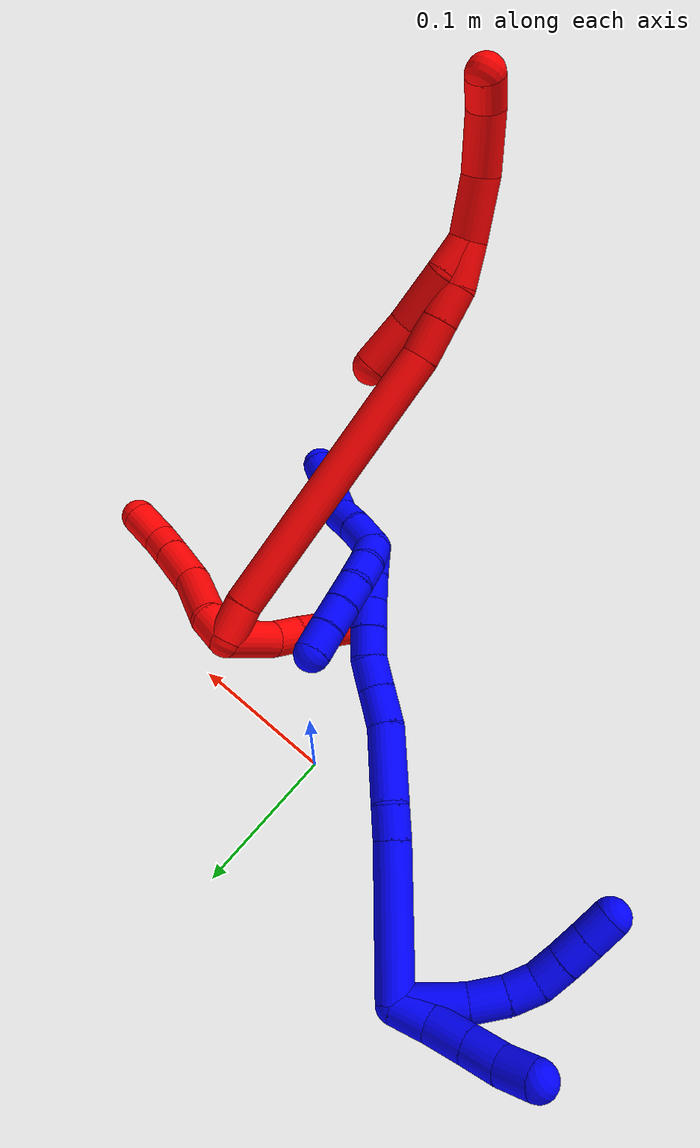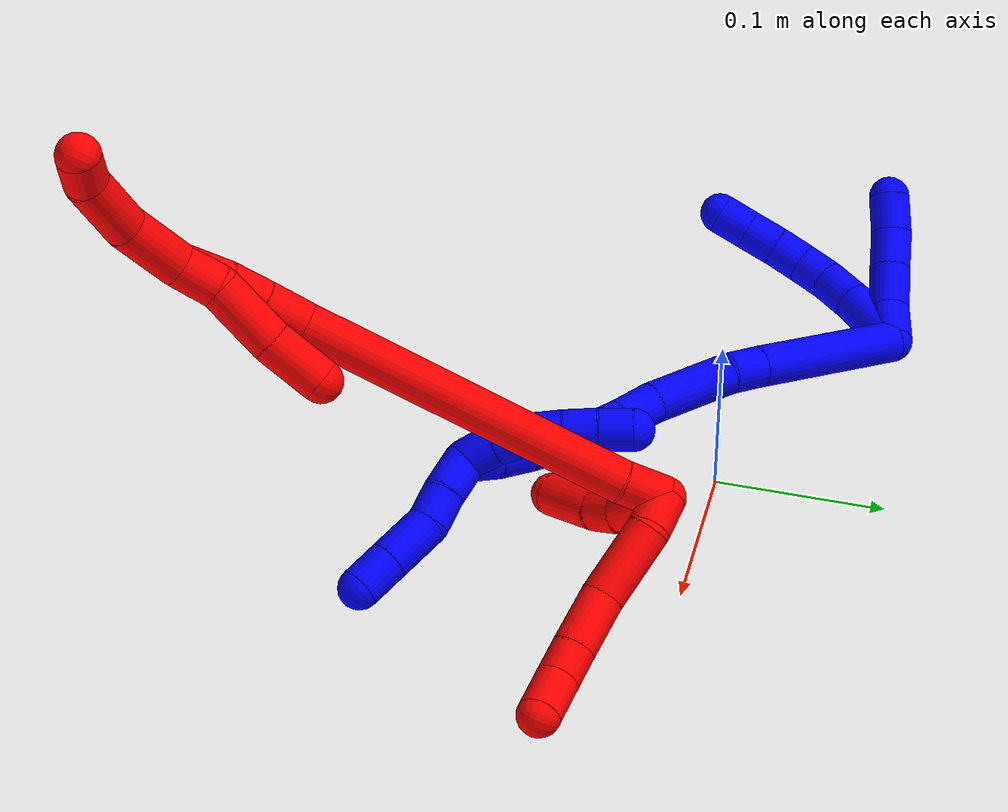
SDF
<sdf version="1.7">
 <world name="default">
  <plugin name="TubeGeneratorPlugin" filename="libtube_generator_plugin.so"/>
  <model name="photoneo_s_sensor">
   <static>1</static>
   <pose>0 0 2 1.57079 1.57079 3.14159</pose>
   <link name="link">
    <inertial><mass>0.1</mass></inertial>
    <sensor name="sensor" type="depth">
     <update_rate>30</update_rate>
     <camera>
      <horizontal_fov>1.22</horizontal_fov>
      <image><width>1920</width><height>1200</height><format>B8G8R8</format></image>
      <clip><near>0.1</near><far>4</far></clip>
      <depth_camera><output>points</output></depth_camera>
     </camera>
     <plugin name="camera_plugin" filename="libgazebo_ros_depth_camera.so">
      <baseline>0.2</baseline>
      <alwaysOn>1</alwaysOn>
      <updateRate>0.0</updateRate>
      <cameraName>camera_ir</cameraName>
      <imageTopicName>/camera/color/image_raw</imageTopicName>
      <cameraInfoTopicName>/camera/color/camera_info</cameraInfoTopicName>
      <depthImageTopicName>/camera/depth/image_raw</depthImageTopicName>
      <depthImageCameraInfoTopicName>/camera/depth/camera_info</depthImageCameraInfoTopicName>
      <pointCloudTopicName>/camera/depth/points</pointCloudTopicName>
      <frameName>fr_optical</frameName>
      <pointCloudCutoff>0.1</pointCloudCutoff>
      <pointCloudCutoffMax>2.0</pointCloudCutoffMax>
      <distortionK1>0</distortionK1>
      <distortionK2>0</distortionK2>
      <distortionK3>0</distortionK3>
      <distortionT1>0</distortionT1>
      <distortionT2>0</distortionT2>
      <CxPrime>0</CxPrime>
      <Cx>0</Cx>
      <Cy>0</Cy>
      <focalLength>0</focalLength>
      <hackBaseline>0</hackBaseline>
     </plugin>
    </sensor>
   </link>
  </model>
  <gravity>0 0 -9.8</gravity>
  <magnetic_field>6e-06 2.3e-05 -4.2e-05</magnetic_field>
  <atmosphere type="adiabatic"/>
  <physics name="default_physics" default="0" type="ode">
   <max_step_size>0.003</max_step_size>
   <real_time_factor>1</real_time_factor>
   <real_time_update_rate>1000</real_time_update_rate>
   <max_contacts>10000</max_contacts>
   <ode>
    <solver>
     <type>quick</type>
     <iters>100</iters>
     <sor>1.3</sor>
     <use_dynamic_moi_rescaling>0</use_dynamic_moi_rescaling>
    </solver>
    <constraints>
     <contact_max_correcting_vel>0</contact_max_correcting_vel>
     <contact_surface_layer>0.001</contact_surface_layer>
     <cfm>0</cfm>
     <erp>0.2</erp>
    </constraints>
   </ode>
  </physics>
  <scene><ambient>0.4 0.4 0.4 1</ambient><background>0.7 0.7 0.7 1</background><shadows>0</shadows></scene>
  <audio><device>default</device></audio>
  <spherical_coordinates>
   <surface_model>EARTH_WGS84</surface_model>
   <latitude_deg>0</latitude_deg>
   <longitude_deg>0</longitude_deg>
   <elevation>0</elevation>
   <heading_deg>0</heading_deg>
  </spherical_coordinates>
  <model name="bin">
   <static>1</static>
   <link name="bottom">
    <collision name="collision-bottom">
     <pose>0 0 -0.01 0 -0 0</pose>
     <geometry><box><size>0.8 0.6 0.02</size></box></geometry>
     <surface>
      <friction><ode><mu>100</mu><mu2>100</mu2></ode></friction>
      <contact><collide_bitmask>65535</collide_bitmask></contact>
     </surface>
    </collision>
   </link>
   <link name="west_wall">
    <collision name="collision-west_wall">
     <pose>-0.41 0 0.1 0 -0 0</pose>
     <geometry><box><size>0.02 0.6 0.2</size></box></geometry>
     <surface>
      <friction><ode><mu>100</mu><mu2>100</mu2></ode></friction>
      <contact><collide_bitmask>65535</collide_bitmask></contact>
     </surface>
    </collision>
   </link>
   <link name="east_wall">
    <collision name="collision-east_wall">
     <pose>0.41 0 0.1 0 -0 0</pose>
     <geometry><box><size>0.02 0.6 0.2</size></box></geometry>
     <surface>
      <friction><ode><mu>100</mu><mu2>100</mu2></ode></friction>
      <contact><collide_bitmask>65535</collide_bitmask></contact>
     </surface>
    </collision>
   </link>
   <link name="south_wall">
    <collision name="collision-south_wall">
     <pose>0 -0.31 0.1 0 -0 0</pose>
     <geometry><box><size>0.8 0.02 0.2</size></box></geometry>
     <surface>
      <friction><ode><mu>100</mu><mu2>100</mu2></ode></friction>
      <contact><collide_bitmask>65535</collide_bitmask></contact>
     </surface>
    </collision>
   </link>
   <link name="north_wall">
    <collision name="collision-north_wall">
     <pose>0 0.31 0.1 0 -0 0</pose>
     <geometry><box><size>0.8 0.02 0.2</size></box></geometry>
     <surface>
      <friction><ode><mu>100</mu><mu2>100</mu2></ode></friction>
      <contact><collide_bitmask>65535</collide_bitmask></contact>
     </surface>
    </collision>
   </link>
  </model>
  <model name="1">
   <static>0</static>
   <link name="1">
    <collision name="collision-cylinder-e_1_2_8">
     <pose>-0.015912 -0.004776 0.014608 0.316004 -0.802785 -0.135045</pose>
     <geometry><cylinder><radius>0.0125</radius><length>0.044245</length></cylinder></geometry>
     <surface>
      <friction><ode><mu>1.16</mu><mu2>1.16</mu2><slip1>0</slip1><slip2>0</slip2></ode></friction>
      <contact><ode><kp>1e+06</kp><kd>1</kd><max_vel>0</max_vel><min_depth>0.001</min_depth></ode></contact>
     </surface>
    </collision>
    <visual name="visual-cylinder-e_1_2_8">
     <pose>-0.015912 -0.004776 0.014608 0.316004 -0.802785 -0.135045</pose>
     <geometry><cylinder><radius>0.0125</radius><length>0.044245</length></cylinder></geometry>
     <material><ambient>0 0 1 1</ambient></material>
    </visual>
    <collision name="collision-cylinder-e_2_8_9">
     <pose>-0.03916 -0.013306 0.038534 0.382971 -0.630667 -0.126314</pose>
     <geometry><cylinder><radius>0.0125</radius><length>0.024878</length></cylinder></geometry>
     <surface>
      <friction><ode><mu>1.16</mu><mu2>1.16</mu2><slip1>0</slip1><slip2>0</slip2></ode></friction>
      <contact><ode><kp>1e+06</kp><kd>1</kd><max_vel>0</max_vel><min_depth>0.001</min_depth></ode></contact>
     </surface>
    </collision>
    <visual name="visual-cylinder-e_2_8_9">
     <pose>-0.03916 -0.013306 0.038534 0.382971 -0.630667 -0.126314</pose>
     <geometry><cylinder><radius>0.0125</radius><length>0.024878</length></cylinder></geometry>
     <material><ambient>0 0 1 1</ambient></material>
    </visual>
    <collision name="collision-cylinder-e_3_9_10">
     <pose>-0.05063 -0.020965 0.056376 0.429572 -0.415326 -0.091864</pose>
     <geometry><cylinder><radius>0.0125</radius><length>0.020494</length></cylinder></geometry>
     <surface>
      <friction><ode><mu>1.16</mu><mu2>1.16</mu2><slip1>0</slip1><slip2>0</slip2></ode></friction>
      <contact><ode><kp>1e+06</kp><kd>1</kd><max_vel>0</max_vel><min_depth>0.001</min_depth></ode></contact>
     </surface>
    </collision>
    <visual name="visual-cylinder-e_3_9_10">
     <pose>-0.05063 -0.020965 0.056376 0.429572 -0.415326 -0.091864</pose>
     <geometry><cylinder><radius>0.0125</radius><length>0.020494</length></cylinder></geometry>
     <material><ambient>0 0 1 1</ambient></material>
    </visual>
    <collision name="collision-cylinder-e_4_10_11">
     <pose>-0.055497 -0.028649 0.074183 0.386614 -0.072952 -0.014287</pose>
     <geometry><cylinder><radius>0.0125</radius><length>0.020099</length></cylinder></geometry>
     <surface>
      <friction><ode><mu>1.16</mu><mu2>1.16</mu2><slip1>0</slip1><slip2>0</slip2></ode></friction>
      <contact><ode><kp>1e+06</kp><kd>1</kd><max_vel>0</max_vel><min_depth>0.001</min_depth></ode></contact>
     </surface>
    </collision>
    <visual name="visual-cylinder-e_4_10_11">
     <pose>-0.055497 -0.028649 0.074183 0.386614 -0.072952 -0.014287</pose>
     <geometry><cylinder><radius>0.0125</radius><length>0.020099</length></cylinder></geometry>
     <material><ambient>0 0 1 1</ambient></material>
    </visual>
    <collision name="collision-cylinder-e_5_11_12">
     <pose>-0.056769 -0.036622 0.092645 0.42859 -0.053484 -0.011643</pose>
     <geometry><cylinder><radius>0.0125</radius><length>0.020213</length></cylinder></geometry>
     <surface>
      <friction><ode><mu>1.16</mu><mu2>1.16</mu2><slip1>0</slip1><slip2>0</slip2></ode></friction>
      <contact><ode><kp>1e+06</kp><kd>1</kd><max_vel>0</max_vel><min_depth>0.001</min_depth></ode></contact>
     </surface>
    </collision>
    <visual name="visual-cylinder-e_5_11_12">
     <pose>-0.056769 -0.036622 0.092645 0.42859 -0.053484 -0.011643</pose>
     <geometry><cylinder><radius>0.0125</radius><length>0.020213</length></cylinder></geometry>
     <material><ambient>0 0 1 1</ambient></material>
    </visual>
    <collision name="collision-cylinder-e_6_12_6">
     <pose>-0.057515 -0.04481 0.111029 0.409349 -0.020416 -0.004238</pose>
     <geometry><cylinder><radius>0.0125</radius><length>0.020071</length></cylinder></geometry>
     <surface>
      <friction><ode><mu>1.16</mu><mu2>1.16</mu2><slip1>0</slip1><slip2>0</slip2></ode></friction>
      <contact><ode><kp>1e+06</kp><kd>1</kd><max_vel>0</max_vel><min_depth>0.001</min_depth></ode></contact>
     </surface>
    </collision>
    <visual name="visual-cylinder-e_6_12_6">
     <pose>-0.057515 -0.04481 0.111029 0.409349 -0.020416 -0.004238</pose>
     <geometry><cylinder><radius>0.0125</radius><length>0.020071</length></cylinder></geometry>
     <material><ambient>0 0 1 1</ambient></material>
    </visual>
    <collision name="collision-cylinder-e_1_2_13">
     <pose>-0.009398 0.003687 0.007187 -0.473967 -0.860828 0.220874</pose>
     <geometry><cylinder><radius>0.0125</radius><length>0.024784</length></cylinder></geometry>
     <surface>
      <friction><ode><mu>1.16</mu><mu2>1.16</mu2><slip1>0</slip1><slip2>0</slip2></ode></friction>
      <contact><ode><kp>1e+06</kp><kd>1</kd><max_vel>0</max_vel><min_depth>0.001</min_depth></ode></contact>
     </surface>
    </collision>
    <visual name="visual-cylinder-e_1_2_13">
     <pose>-0.009398 0.003687 0.007187 -0.473967 -0.860828 0.220874</pose>
     <geometry><cylinder><radius>0.0125</radius><length>0.024784</length></cylinder></geometry>
     <material><ambient>0 0 1 1</ambient></material>
    </visual>
    <collision name="collision-cylinder-e_2_13_14">
     <pose>-0.026816 0.013936 0.02366 -0.615197 -0.614237 0.20083</pose>
     <geometry><cylinder><radius>0.0125</radius><length>0.02783</length></cylinder></geometry>
     <surface>
      <friction><ode><mu>1.16</mu><mu2>1.16</mu2><slip1>0</slip1><slip2>0</slip2></ode></friction>
      <contact><ode><kp>1e+06</kp><kd>1</kd><max_vel>0</max_vel><min_depth>0.001</min_depth></ode></contact>
     </surface>
    </collision>
    <visual name="visual-cylinder-e_2_13_14">
     <pose>-0.026816 0.013936 0.02366 -0.615197 -0.614237 0.20083</pose>
     <geometry><cylinder><radius>0.0125</radius><length>0.02783</length></cylinder></geometry>
     <material><ambient>0 0 1 1</ambient></material>
    </visual>
    <collision name="collision-cylinder-e_3_14_15">
     <pose>-0.04117 0.026561 0.041048 -0.642407 -0.559346 0.190539</pose>
     <geometry><cylinder><radius>0.0125</radius><length>0.023876</length></cylinder></geometry>
     <surface>
      <friction><ode><mu>1.16</mu><mu2>1.16</mu2><slip1>0</slip1><slip2>0</slip2></ode></friction>
      <contact><ode><kp>1e+06</kp><kd>1</kd><max_vel>0</max_vel><min_depth>0.001</min_depth></ode></contact>
     </surface>
    </collision>
    <visual name="visual-cylinder-e_3_14_15">
     <pose>-0.04117 0.026561 0.041048 -0.642407 -0.559346 0.190539</pose>
     <geometry><cylinder><radius>0.0125</radius><length>0.023876</length></cylinder></geometry>
     <material><ambient>0 0 1 1</ambient></material>
    </visual>
    <collision name="collision-cylinder-e_4_15_5">
     <pose>-0.052242 0.038118 0.058399 -0.536062 -0.414777 0.115447</pose>
     <geometry><cylinder><radius>0.0125</radius><length>0.02351</length></cylinder></geometry>
     <surface>
      <friction><ode><mu>1.16</mu><mu2>1.16</mu2><slip1>0</slip1><slip2>0</slip2></ode></friction>
      <contact><ode><kp>1e+06</kp><kd>1</kd><max_vel>0</max_vel><min_depth>0.001</min_depth></ode></contact>
     </surface>
    </collision>
    <visual name="visual-cylinder-e_4_15_5">
     <pose>-0.052242 0.038118 0.058399 -0.536062 -0.414777 0.115447</pose>
     <geometry><cylinder><radius>0.0125</radius><length>0.02351</length></cylinder></geometry>
     <material><ambient>0 0 1 1</ambient></material>
    </visual>
    <collision name="collision-cylinder-e_1_2_16">
     <pose>0.028837 -0.0329 0.020781 1.00742 0.637754 0.359967</pose>
     <geometry><cylinder><radius>0.0125</radius><length>0.096867</length></cylinder></geometry>
     <surface>
      <friction><ode><mu>1.16</mu><mu2>1.16</mu2><slip1>0</slip1><slip2>0</slip2></ode></friction>
      <contact><ode><kp>1e+06</kp><kd>1</kd><max_vel>0</max_vel><min_depth>0.001</min_depth></ode></contact>
     </surface>
    </collision>
    <visual name="visual-cylinder-e_1_2_16">
     <pose>0.028837 -0.0329 0.020781 1.00742 0.637754 0.359967</pose>
     <geometry><cylinder><radius>0.0125</radius><length>0.096867</length></cylinder></geometry>
     <material><ambient>0 0 1 1</ambient></material>
    </visual>
    <collision name="collision-cylinder-e_2_16_17">
     <pose>0.06464 -0.073272 0.046001 1.03483 0.675622 0.394644</pose>
     <geometry><cylinder><radius>0.0125</radius><length>0.022279</length></cylinder></geometry>
     <surface>
      <friction><ode><mu>1.16</mu><mu2>1.16</mu2><slip1>0</slip1><slip2>0</slip2></ode></friction>
      <contact><ode><kp>1e+06</kp><kd>1</kd><max_vel>0</max_vel><min_depth>0.001</min_depth></ode></contact>
     </surface>
    </collision>
    <visual name="visual-cylinder-e_2_16_17">
     <pose>0.06464 -0.073272 0.046001 1.03483 0.675622 0.394644</pose>
     <geometry><cylinder><radius>0.0125</radius><length>0.022279</length></cylinder></geometry>
     <material><ambient>0 0 1 1</ambient></material>
    </visual>
    <collision name="collision-cylinder-e_3_17_18">
     <pose>0.08564 -0.101373 0.057855 1.22573 0.569464 0.40596</pose>
     <geometry><cylinder><radius>0.0125</radius><length>0.052054</length></cylinder></geometry>
     <surface>
      <friction><ode><mu>1.16</mu><mu2>1.16</mu2><slip1>0</slip1><slip2>0</slip2></ode></friction>
      <contact><ode><kp>1e+06</kp><kd>1</kd><max_vel>0</max_vel><min_depth>0.001</min_depth></ode></contact>
     </surface>
    </collision>
    <visual name="visual-cylinder-e_3_17_18">
     <pose>0.08564 -0.101373 0.057855 1.22573 0.569464 0.40596</pose>
     <geometry><cylinder><radius>0.0125</radius><length>0.052054</length></cylinder></geometry>
     <material><ambient>0 0 1 1</ambient></material>
    </visual>
    <collision name="collision-cylinder-e_4_18_19">
     <pose>0.108608 -0.131469 0.067616 1.32785 0.741528 0.590535</pose>
     <geometry><cylinder><radius>0.0125</radius><length>0.026456</length></cylinder></geometry>
     <surface>
      <friction><ode><mu>1.16</mu><mu2>1.16</mu2><slip1>0</slip1><slip2>0</slip2></ode></friction>
      <contact><ode><kp>1e+06</kp><kd>1</kd><max_vel>0</max_vel><min_depth>0.001</min_depth></ode></contact>
     </surface>
    </collision>
    <visual name="visual-cylinder-e_4_18_19">
     <pose>0.108608 -0.131469 0.067616 1.32785 0.741528 0.590535</pose>
     <geometry><cylinder><radius>0.0125</radius><length>0.026456</length></cylinder></geometry>
     <material><ambient>0 0 1 1</ambient></material>
    </visual>
    <collision name="collision-cylinder-e_5_19_20">
     <pose>0.125314 -0.147959 0.072515 1.22204 0.805138 0.579727</pose>
     <geometry><cylinder><radius>0.0125</radius><length>0.021561</length></cylinder></geometry>
     <surface>
      <friction><ode><mu>1.16</mu><mu2>1.16</mu2><slip1>0</slip1><slip2>0</slip2></ode></friction>
      <contact><ode><kp>1e+06</kp><kd>1</kd><max_vel>0</max_vel><min_depth>0.001</min_depth></ode></contact>
     </surface>
    </collision>
    <visual name="visual-cylinder-e_5_19_20">
     <pose>0.125314 -0.147959 0.072515 1.22204 0.805138 0.579727</pose>
     <geometry><cylinder><radius>0.0125</radius><length>0.021561</length></cylinder></geometry>
     <material><ambient>0 0 1 1</ambient></material>
    </visual>
    <collision name="collision-cylinder-e_6_20_21">
     <pose>0.138848 -0.162497 0.07902 1.08675 0.596194 0.367002</pose>
     <geometry><cylinder><radius>0.0125</radius><length>0.020525</length></cylinder></geometry>
     <surface>
      <friction><ode><mu>1.16</mu><mu2>1.16</mu2><slip1>0</slip1><slip2>0</slip2></ode></friction>
      <contact><ode><kp>1e+06</kp><kd>1</kd><max_vel>0</max_vel><min_depth>0.001</min_depth></ode></contact>
     </surface>
    </collision>
    <visual name="visual-cylinder-e_6_20_21">
     <pose>0.138848 -0.162497 0.07902 1.08675 0.596194 0.367002</pose>
     <geometry><cylinder><radius>0.0125</radius><length>0.020525</length></cylinder></geometry>
     <material><ambient>0 0 1 1</ambient></material>
    </visual>
    <collision name="collision-cylinder-e_7_21_22">
     <pose>0.14989 -0.177762 0.086707 1.12165 0.550464 0.351096</pose>
     <geometry><cylinder><radius>0.0125</radius><length>0.020186</length></cylinder></geometry>
     <surface>
      <friction><ode><mu>1.16</mu><mu2>1.16</mu2><slip1>0</slip1><slip2>0</slip2></ode></friction>
      <contact><ode><kp>1e+06</kp><kd>1</kd><max_vel>0</max_vel><min_depth>0.001</min_depth></ode></contact>
     </surface>
    </collision>
    <visual name="visual-cylinder-e_7_21_22">
     <pose>0.14989 -0.177762 0.086707 1.12165 0.550464 0.351096</pose>
     <geometry><cylinder><radius>0.0125</radius><length>0.020186</length></cylinder></geometry>
     <material><ambient>0 0 1 1</ambient></material>
    </visual>
    <collision name="collision-cylinder-e_8_22_23">
     <pose>0.160383 -0.192991 0.094571 1.06647 0.547936 0.328779</pose>
     <geometry><cylinder><radius>0.0125</radius><length>0.020018</length></cylinder></geometry>
     <surface>
      <friction><ode><mu>1.16</mu><mu2>1.16</mu2><slip1>0</slip1><slip2>0</slip2></ode></friction>
      <contact><ode><kp>1e+06</kp><kd>1</kd><max_vel>0</max_vel><min_depth>0.001</min_depth></ode></contact>
     </surface>
    </collision>
    <visual name="visual-cylinder-e_8_22_23">
     <pose>0.160383 -0.192991 0.094571 1.06647 0.547936 0.328779</pose>
     <geometry><cylinder><radius>0.0125</radius><length>0.020018</length></cylinder></geometry>
     <material><ambient>0 0 1 1</ambient></material>
    </visual>
    <collision name="collision-cylinder-e_9_23_1">
     <pose>0.170892 -0.207261 0.103837 0.923031 0.556261 0.282125</pose>
     <geometry><cylinder><radius>0.0125</radius><length>0.020055</length></cylinder></geometry>
     <surface>
      <friction><ode><mu>1.16</mu><mu2>1.16</mu2><slip1>0</slip1><slip2>0</slip2></ode></friction>
      <contact><ode><kp>1e+06</kp><kd>1</kd><max_vel>0</max_vel><min_depth>0.001</min_depth></ode></contact>
     </surface>
    </collision>
    <visual name="visual-cylinder-e_9_23_1">
     <pose>0.170892 -0.207261 0.103837 0.923031 0.556261 0.282125</pose>
     <geometry><cylinder><radius>0.0125</radius><length>0.020055</length></cylinder></geometry>
     <material><ambient>0 0 1 1</ambient></material>
    </visual>
    <collision name="collision-cylinder-e_1_1_24">
     <pose>0.184296 -0.22275 0.105665 1.93451 0.716797 0.995487</pose>
     <geometry><cylinder><radius>0.0125</radius><length>0.024689</length></cylinder></geometry>
     <surface>
      <friction><ode><mu>1.16</mu><mu2>1.16</mu2><slip1>0</slip1><slip2>0</slip2></ode></friction>
      <contact><ode><kp>1e+06</kp><kd>1</kd><max_vel>0</max_vel><min_depth>0.001</min_depth></ode></contact>
     </surface>
    </collision>
    <visual name="visual-cylinder-e_1_1_24">
     <pose>0.184296 -0.22275 0.105665 1.93451 0.716797 0.995487</pose>
     <geometry><cylinder><radius>0.0125</radius><length>0.024689</length></cylinder></geometry>
     <material><ambient>0 0 1 1</ambient></material>
    </visual>
    <collision name="collision-cylinder-e_2_24_25">
     <pose>0.198352 -0.238749 0.098493 2.05725 0.623964 0.983121</pose>
     <geometry><cylinder><radius>0.0125</radius><length>0.020355</length></cylinder></geometry>
     <surface>
      <friction><ode><mu>1.16</mu><mu2>1.16</mu2><slip1>0</slip1><slip2>0</slip2></ode></friction>
      <contact><ode><kp>1e+06</kp><kd>1</kd><max_vel>0</max_vel><min_depth>0.001</min_depth></ode></contact>
     </surface>
    </collision>
    <visual name="visual-cylinder-e_2_24_25">
     <pose>0.198352 -0.238749 0.098493 2.05725 0.623964 0.983121</pose>
     <geometry><cylinder><radius>0.0125</radius><length>0.020355</length></cylinder></geometry>
     <material><ambient>0 0 1 1</ambient></material>
    </visual>
    <collision name="collision-cylinder-e_3_25_26">
     <pose>0.213291 -0.259087 0.093439 1.66203 0.601919 0.655623</pose>
     <geometry><cylinder><radius>0.0125</radius><length>0.031764</length></cylinder></geometry>
     <surface>
      <friction><ode><mu>1.16</mu><mu2>1.16</mu2><slip1>0</slip1><slip2>0</slip2></ode></friction>
      <contact><ode><kp>1e+06</kp><kd>1</kd><max_vel>0</max_vel><min_depth>0.001</min_depth></ode></contact>
     </surface>
    </collision>
    <visual name="visual-cylinder-e_3_25_26">
     <pose>0.213291 -0.259087 0.093439 1.66203 0.601919 0.655623</pose>
     <geometry><cylinder><radius>0.0125</radius><length>0.031764</length></cylinder></geometry>
     <material><ambient>0 0 1 1</ambient></material>
    </visual>
    <collision name="collision-cylinder-e_4_26_4">
     <pose>0.228702 -0.281738 0.091339 1.6649 0.586528 0.640763</pose>
     <geometry><cylinder><radius>0.0125</radius><length>0.023192</length></cylinder></geometry>
     <surface>
      <friction><ode><mu>1.16</mu><mu2>1.16</mu2><slip1>0</slip1><slip2>0</slip2></ode></friction>
      <contact><ode><kp>1e+06</kp><kd>1</kd><max_vel>0</max_vel><min_depth>0.001</min_depth></ode></contact>
     </surface>
    </collision>
    <visual name="visual-cylinder-e_4_26_4">
     <pose>0.228702 -0.281738 0.091339 1.6649 0.586528 0.640763</pose>
     <geometry><cylinder><radius>0.0125</radius><length>0.023192</length></cylinder></geometry>
     <material><ambient>0 0 1 1</ambient></material>
    </visual>
    <collision name="collision-cylinder-e_1_1_27">
     <pose>0.175727 -0.204126 0.107846 -1.6841 -0.045977 0.051503</pose>
     <geometry><cylinder><radius>0.0125</radius><length>0.02</length></cylinder></geometry>
     <surface>
      <friction><ode><mu>1.16</mu><mu2>1.16</mu2><slip1>0</slip1><slip2>0</slip2></ode></friction>
      <contact><ode><kp>1e+06</kp><kd>1</kd><max_vel>0</max_vel><min_depth>0.001</min_depth></ode></contact>
     </surface>
    </collision>
    <visual name="visual-cylinder-e_1_1_27">
     <pose>0.175727 -0.204126 0.107846 -1.6841 -0.045977 0.051503</pose>
     <geometry><cylinder><radius>0.0125</radius><length>0.02</length></cylinder></geometry>
     <material><ambient>0 0 1 1</ambient></material>
    </visual>
    <collision name="collision-cylinder-e_2_27_28">
     <pose>0.174944 -0.184752 0.103458 -1.9029 -0.032357 0.045382</pose>
     <geometry><cylinder><radius>0.0125</radius><length>0.02</length></cylinder></geometry>
     <surface>
      <friction><ode><mu>1.16</mu><mu2>1.16</mu2><slip1>0</slip1><slip2>0</slip2></ode></friction>
      <contact><ode><kp>1e+06</kp><kd>1</kd><max_vel>0</max_vel><min_depth>0.001</min_depth></ode></contact>
     </surface>
    </collision>
    <visual name="visual-cylinder-e_2_27_28">
     <pose>0.174944 -0.184752 0.103458 -1.9029 -0.032357 0.045382</pose>
     <geometry><cylinder><radius>0.0125</radius><length>0.02</length></cylinder></geometry>
     <material><ambient>0 0 1 1</ambient></material>
    </visual>
    <collision name="collision-cylinder-e_3_28_29">
     <pose>0.173962 -0.166655 0.095224 -2.09288 -0.065865 0.113801</pose>
     <geometry><cylinder><radius>0.0125</radius><length>0.02</length></cylinder></geometry>
     <surface>
      <friction><ode><mu>1.16</mu><mu2>1.16</mu2><slip1>0</slip1><slip2>0</slip2></ode></friction>
      <contact><ode><kp>1e+06</kp><kd>1</kd><max_vel>0</max_vel><min_depth>0.001</min_depth></ode></contact>
     </surface>
    </collision>
    <visual name="visual-cylinder-e_3_28_29">
     <pose>0.173962 -0.166655 0.095224 -2.09288 -0.065865 0.113801</pose>
     <geometry><cylinder><radius>0.0125</radius><length>0.02</length></cylinder></geometry>
     <material><ambient>0 0 1 1</ambient></material>
    </visual>
    <collision name="collision-cylinder-e_4_29_30">
     <pose>0.172545 -0.149632 0.084833 -2.14477 -0.075924 0.139345</pose>
     <geometry><cylinder><radius>0.0125</radius><length>0.02</length></cylinder></geometry>
     <surface>
      <friction><ode><mu>1.16</mu><mu2>1.16</mu2><slip1>0</slip1><slip2>0</slip2></ode></friction>
      <contact><ode><kp>1e+06</kp><kd>1</kd><max_vel>0</max_vel><min_depth>0.001</min_depth></ode></contact>
     </surface>
    </collision>
    <visual name="visual-cylinder-e_4_29_30">
     <pose>0.172545 -0.149632 0.084833 -2.14477 -0.075924 0.139345</pose>
     <geometry><cylinder><radius>0.0125</radius><length>0.02</length></cylinder></geometry>
     <material><ambient>0 0 1 1</ambient></material>
    </visual>
    <collision name="collision-cylinder-e_5_30_3">
     <pose>0.170691 -0.133307 0.073456 -2.21421 -0.109799 0.218915</pose>
     <geometry><cylinder><radius>0.0125</radius><length>0.02</length></cylinder></geometry>
     <surface>
      <friction><ode><mu>1.16</mu><mu2>1.16</mu2><slip1>0</slip1><slip2>0</slip2></ode></friction>
      <contact><ode><kp>1e+06</kp><kd>1</kd><max_vel>0</max_vel><min_depth>0.001</min_depth></ode></contact>
     </surface>
    </collision>
    <visual name="visual-cylinder-e_5_30_3">
     <pose>0.170691 -0.133307 0.073456 -2.21421 -0.109799 0.218915</pose>
     <geometry><cylinder><radius>0.0125</radius><length>0.02</length></cylinder></geometry>
     <material><ambient>0 0 1 1</ambient></material>
    </visual>
    <collision name="collision-sphere-3">
     <pose>0.169595 -0.125354 0.067493 0 -0 0</pose>
     <geometry><sphere><radius>0.0125</radius></sphere></geometry>
     <surface>
      <friction><ode><mu>1.16</mu><mu2>1.16</mu2><slip1>0</slip1><slip2>0</slip2></ode></friction>
      <contact><ode><kp>1e+06</kp><kd>1</kd><max_vel>0</max_vel><min_depth>0.001</min_depth></ode></contact>
     </surface>
    </collision>
    <visual name="visual-sphere-3">
     <pose>0.169595 -0.125354 0.067493 0 -0 0</pose>
     <geometry><sphere><radius>0.0125</radius></sphere></geometry>
     <material><ambient>0 0 1 1</ambient></material>
    </visual>
    <collision name="collision-sphere-30">
     <pose>0.171787 -0.141259 0.079419 0 -0 0</pose>
     <geometry><sphere><radius>0.0125</radius></sphere></geometry>
     <surface>
      <friction><ode><mu>1.16</mu><mu2>1.16</mu2><slip1>0</slip1><slip2>0</slip2></ode></friction>
      <contact><ode><kp>1e+06</kp><kd>1</kd><max_vel>0</max_vel><min_depth>0.001</min_depth></ode></contact>
     </surface>
    </collision>
    <visual name="visual-sphere-30">
     <pose>0.171787 -0.141259 0.079419 0 -0 0</pose>
     <geometry><sphere><radius>0.0125</radius></sphere></geometry>
     <material><ambient>0 0 1 1</ambient></material>
    </visual>
    <collision name="collision-sphere-29">
     <pose>0.173304 -0.158006 0.090248 0 -0 0</pose>
     <geometry><sphere><radius>0.0125</radius></sphere></geometry>
     <surface>
      <friction><ode><mu>1.16</mu><mu2>1.16</mu2><slip1>0</slip1><slip2>0</slip2></ode></friction>
      <contact><ode><kp>1e+06</kp><kd>1</kd><max_vel>0</max_vel><min_depth>0.001</min_depth></ode></contact>
     </surface>
    </collision>
    <visual name="visual-sphere-29">
     <pose>0.173304 -0.158006 0.090248 0 -0 0</pose>
     <geometry><sphere><radius>0.0125</radius></sphere></geometry>
     <material><ambient>0 0 1 1</ambient></material>
    </visual>
    <collision name="collision-sphere-28">
     <pose>0.17462 -0.175304 0.1002 0 -0 0</pose>
     <geometry><sphere><radius>0.0125</radius></sphere></geometry>
     <surface>
      <friction><ode><mu>1.16</mu><mu2>1.16</mu2><slip1>0</slip1><slip2>0</slip2></ode></friction>
      <contact><ode><kp>1e+06</kp><kd>1</kd><max_vel>0</max_vel><min_depth>0.001</min_depth></ode></contact>
     </surface>
    </collision>
    <visual name="visual-sphere-28">
     <pose>0.17462 -0.175304 0.1002 0 -0 0</pose>
     <geometry><sphere><radius>0.0125</radius></sphere></geometry>
     <material><ambient>0 0 1 1</ambient></material>
    </visual>
    <collision name="collision-sphere-27">
     <pose>0.175267 -0.194201 0.106717 0 -0 0</pose>
     <geometry><sphere><radius>0.0125</radius></sphere></geometry>
     <surface>
      <friction><ode><mu>1.16</mu><mu2>1.16</mu2><slip1>0</slip1><slip2>0</slip2></ode></friction>
      <contact><ode><kp>1e+06</kp><kd>1</kd><max_vel>0</max_vel><min_depth>0.001</min_depth></ode></contact>
     </surface>
    </collision>
    <visual name="visual-sphere-27">
     <pose>0.175267 -0.194201 0.106717 0 -0 0</pose>
     <geometry><sphere><radius>0.0125</radius></sphere></geometry>
     <material><ambient>0 0 1 1</ambient></material>
    </visual>
    <collision name="collision-sphere-4">
     <pose>0.235121 -0.291354 0.090431 0 -0 0</pose>
     <geometry><sphere><radius>0.0125</radius></sphere></geometry>
     <surface>
      <friction><ode><mu>1.16</mu><mu2>1.16</mu2><slip1>0</slip1><slip2>0</slip2></ode></friction>
      <contact><ode><kp>1e+06</kp><kd>1</kd><max_vel>0</max_vel><min_depth>0.001</min_depth></ode></contact>
     </surface>
    </collision>
    <visual name="visual-sphere-4">
     <pose>0.235121 -0.291354 0.090431 0 -0 0</pose>
     <geometry><sphere><radius>0.0125</radius></sphere></geometry>
     <material><ambient>0 0 1 1</ambient></material>
    </visual>
    <collision name="collision-sphere-26">
     <pose>0.222284 -0.272123 0.092246 0 -0 0</pose>
     <geometry><sphere><radius>0.0125</radius></sphere></geometry>
     <surface>
      <friction><ode><mu>1.16</mu><mu2>1.16</mu2><slip1>0</slip1><slip2>0</slip2></ode></friction>
      <contact><ode><kp>1e+06</kp><kd>1</kd><max_vel>0</max_vel><min_depth>0.001</min_depth></ode></contact>
     </surface>
    </collision>
    <visual name="visual-sphere-26">
     <pose>0.222284 -0.272123 0.092246 0 -0 0</pose>
     <geometry><sphere><radius>0.0125</radius></sphere></geometry>
     <material><ambient>0 0 1 1</ambient></material>
    </visual>
    <collision name="collision-sphere-25">
     <pose>0.204298 -0.24605 0.094632 0 -0 0</pose>
     <geometry><sphere><radius>0.0125</radius></sphere></geometry>
     <surface>
      <friction><ode><mu>1.16</mu><mu2>1.16</mu2><slip1>0</slip1><slip2>0</slip2></ode></friction>
      <contact><ode><kp>1e+06</kp><kd>1</kd><max_vel>0</max_vel><min_depth>0.001</min_depth></ode></contact>
     </surface>
    </collision>
    <visual name="visual-sphere-25">
     <pose>0.204298 -0.24605 0.094632 0 -0 0</pose>
     <geometry><sphere><radius>0.0125</radius></sphere></geometry>
     <material><ambient>0 0 1 1</ambient></material>
    </visual>
    <collision name="collision-sphere-24">
     <pose>0.192406 -0.231447 0.102354 0 -0 0</pose>
     <geometry><sphere><radius>0.0125</radius></sphere></geometry>
     <surface>
      <friction><ode><mu>1.16</mu><mu2>1.16</mu2><slip1>0</slip1><slip2>0</slip2></ode></friction>
      <contact><ode><kp>1e+06</kp><kd>1</kd><max_vel>0</max_vel><min_depth>0.001</min_depth></ode></contact>
     </surface>
    </collision>
    <visual name="visual-sphere-24">
     <pose>0.192406 -0.231447 0.102354 0 -0 0</pose>
     <geometry><sphere><radius>0.0125</radius></sphere></geometry>
     <material><ambient>0 0 1 1</ambient></material>
    </visual>
    <collision name="collision-sphere-1">
     <pose>0.176186 -0.214052 0.108976 0 -0 0</pose>
     <geometry><sphere><radius>0.0125</radius></sphere></geometry>
     <surface>
      <friction><ode><mu>1.16</mu><mu2>1.16</mu2><slip1>0</slip1><slip2>0</slip2></ode></friction>
      <contact><ode><kp>1e+06</kp><kd>1</kd><max_vel>0</max_vel><min_depth>0.001</min_depth></ode></contact>
     </surface>
    </collision>
    <visual name="visual-sphere-1">
     <pose>0.176186 -0.214052 0.108976 0 -0 0</pose>
     <geometry><sphere><radius>0.0125</radius></sphere></geometry>
     <material><ambient>0 0 1 1</ambient></material>
    </visual>
    <collision name="collision-sphere-23">
     <pose>0.165597 -0.200471 0.098699 0 -0 0</pose>
     <geometry><sphere><radius>0.0125</radius></sphere></geometry>
     <surface>
      <friction><ode><mu>1.16</mu><mu2>1.16</mu2><slip1>0</slip1><slip2>0</slip2></ode></friction>
      <contact><ode><kp>1e+06</kp><kd>1</kd><max_vel>0</max_vel><min_depth>0.001</min_depth></ode></contact>
     </surface>
    </collision>
    <visual name="visual-sphere-23">
     <pose>0.165597 -0.200471 0.098699 0 -0 0</pose>
     <geometry><sphere><radius>0.0125</radius></sphere></geometry>
     <material><ambient>0 0 1 1</ambient></material>
    </visual>
    <collision name="collision-sphere-22">
     <pose>0.155169 -0.185511 0.090442 0 -0 0</pose>
     <geometry><sphere><radius>0.0125</radius></sphere></geometry>
     <surface>
      <friction><ode><mu>1.16</mu><mu2>1.16</mu2><slip1>0</slip1><slip2>0</slip2></ode></friction>
      <contact><ode><kp>1e+06</kp><kd>1</kd><max_vel>0</max_vel><min_depth>0.001</min_depth></ode></contact>
     </surface>
    </collision>
    <visual name="visual-sphere-22">
     <pose>0.155169 -0.185511 0.090442 0 -0 0</pose>
     <geometry><sphere><radius>0.0125</radius></sphere></geometry>
     <material><ambient>0 0 1 1</ambient></material>
    </visual>
    <collision name="collision-sphere-21">
     <pose>0.14461 -0.170013 0.082972 0 -0 0</pose>
     <geometry><sphere><radius>0.0125</radius></sphere></geometry>
     <surface>
      <friction><ode><mu>1.16</mu><mu2>1.16</mu2><slip1>0</slip1><slip2>0</slip2></ode></friction>
      <contact><ode><kp>1e+06</kp><kd>1</kd><max_vel>0</max_vel><min_depth>0.001</min_depth></ode></contact>
     </surface>
    </collision>
    <visual name="visual-sphere-21">
     <pose>0.14461 -0.170013 0.082972 0 -0 0</pose>
     <geometry><sphere><radius>0.0125</radius></sphere></geometry>
     <material><ambient>0 0 1 1</ambient></material>
    </visual>
    <collision name="collision-sphere-12">
     <pose>-0.05731 -0.040817 0.101825 0 -0 0</pose>
     <geometry><sphere><radius>0.0125</radius></sphere></geometry>
     <surface>
      <friction><ode><mu>1.16</mu><mu2>1.16</mu2><slip1>0</slip1><slip2>0</slip2></ode></friction>
      <contact><ode><kp>1e+06</kp><kd>1</kd><max_vel>0</max_vel><min_depth>0.001</min_depth></ode></contact>
     </surface>
    </collision>
    <visual name="visual-sphere-12">
     <pose>-0.05731 -0.040817 0.101825 0 -0 0</pose>
     <geometry><sphere><radius>0.0125</radius></sphere></geometry>
     <material><ambient>0 0 1 1</ambient></material>
    </visual>
    <collision name="collision-sphere-11">
     <pose>-0.056229 -0.032428 0.083466 0 -0 0</pose>
     <geometry><sphere><radius>0.0125</radius></sphere></geometry>
     <surface>
      <friction><ode><mu>1.16</mu><mu2>1.16</mu2><slip1>0</slip1><slip2>0</slip2></ode></friction>
      <contact><ode><kp>1e+06</kp><kd>1</kd><max_vel>0</max_vel><min_depth>0.001</min_depth></ode></contact>
     </surface>
    </collision>
    <visual name="visual-sphere-11">
     <pose>-0.056229 -0.032428 0.083466 0 -0 0</pose>
     <geometry><sphere><radius>0.0125</radius></sphere></geometry>
     <material><ambient>0 0 1 1</ambient></material>
    </visual>
    <collision name="collision-sphere-10">
     <pose>-0.054764 -0.02487 0.0649 0 -0 0</pose>
     <geometry><sphere><radius>0.0125</radius></sphere></geometry>
     <surface>
      <friction><ode><mu>1.16</mu><mu2>1.16</mu2><slip1>0</slip1><slip2>0</slip2></ode></friction>
      <contact><ode><kp>1e+06</kp><kd>1</kd><max_vel>0</max_vel><min_depth>0.001</min_depth></ode></contact>
     </surface>
    </collision>
    <visual name="visual-sphere-10">
     <pose>-0.054764 -0.02487 0.0649 0 -0 0</pose>
     <geometry><sphere><radius>0.0125</radius></sphere></geometry>
     <material><ambient>0 0 1 1</ambient></material>
    </visual>
    <collision name="collision-sphere-9">
     <pose>-0.046495 -0.01706 0.047852 0 -0 0</pose>
     <geometry><sphere><radius>0.0125</radius></sphere></geometry>
     <surface>
      <friction><ode><mu>1.16</mu><mu2>1.16</mu2><slip1>0</slip1><slip2>0</slip2></ode></friction>
      <contact><ode><kp>1e+06</kp><kd>1</kd><max_vel>0</max_vel><min_depth>0.001</min_depth></ode></contact>
     </surface>
    </collision>
    <visual name="visual-sphere-9">
     <pose>-0.046495 -0.01706 0.047852 0 -0 0</pose>
     <geometry><sphere><radius>0.0125</radius></sphere></geometry>
     <material><ambient>0 0 1 1</ambient></material>
    </visual>
    <collision name="collision-sphere-2">
     <geometry><sphere><radius>0.0125</radius></sphere></geometry>
     <surface>
      <friction><ode><mu>1.16</mu><mu2>1.16</mu2><slip1>0</slip1><slip2>0</slip2></ode></friction>
      <contact><ode><kp>1e+06</kp><kd>1</kd><max_vel>0</max_vel><min_depth>0.001</min_depth></ode></contact>
     </surface>
    </collision>
    <visual name="visual-sphere-2">
     <geometry><sphere><radius>0.0125</radius></sphere></geometry>
     <material><ambient>0 0 1 1</ambient></material>
    </visual>
    <collision name="collision-sphere-19">
     <pose>0.117542 -0.140938 0.069962 0 -0 0</pose>
     <geometry><sphere><radius>0.0125</radius></sphere></geometry>
     <surface>
      <friction><ode><mu>1.16</mu><mu2>1.16</mu2><slip1>0</slip1><slip2>0</slip2></ode></friction>
      <contact><ode><kp>1e+06</kp><kd>1</kd><max_vel>0</max_vel><min_depth>0.001</min_depth></ode></contact>
     </surface>
    </collision>
    <visual name="visual-sphere-19">
     <pose>0.117542 -0.140938 0.069962 0 -0 0</pose>
     <geometry><sphere><radius>0.0125</radius></sphere></geometry>
     <material><ambient>0 0 1 1</ambient></material>
    </visual>
    <collision name="collision-sphere-8">
     <pose>-0.031825 -0.009552 0.029215 0 -0 0</pose>
     <geometry><sphere><radius>0.0125</radius></sphere></geometry>
     <surface>
      <friction><ode><mu>1.16</mu><mu2>1.16</mu2><slip1>0</slip1><slip2>0</slip2></ode></friction>
      <contact><ode><kp>1e+06</kp><kd>1</kd><max_vel>0</max_vel><min_depth>0.001</min_depth></ode></contact>
     </surface>
    </collision>
    <visual name="visual-sphere-8">
     <pose>-0.031825 -0.009552 0.029215 0 -0 0</pose>
     <geometry><sphere><radius>0.0125</radius></sphere></geometry>
     <material><ambient>0 0 1 1</ambient></material>
    </visual>
    <collision name="collision-sphere-6">
     <pose>-0.057719 -0.048803 0.120234 0 -0 0</pose>
     <geometry><sphere><radius>0.0125</radius></sphere></geometry>
     <surface>
      <friction><ode><mu>1.16</mu><mu2>1.16</mu2><slip1>0</slip1><slip2>0</slip2></ode></friction>
      <contact><ode><kp>1e+06</kp><kd>1</kd><max_vel>0</max_vel><min_depth>0.001</min_depth></ode></contact>
     </surface>
    </collision>
    <visual name="visual-sphere-6">
     <pose>-0.057719 -0.048803 0.120234 0 -0 0</pose>
     <geometry><sphere><radius>0.0125</radius></sphere></geometry>
     <material><ambient>0 0 1 1</ambient></material>
    </visual>
    <collision name="collision-sphere-13">
     <pose>-0.018796 0.007373 0.014374 0 -0 0</pose>
     <geometry><sphere><radius>0.0125</radius></sphere></geometry>
     <surface>
      <friction><ode><mu>1.16</mu><mu2>1.16</mu2><slip1>0</slip1><slip2>0</slip2></ode></friction>
      <contact><ode><kp>1e+06</kp><kd>1</kd><max_vel>0</max_vel><min_depth>0.001</min_depth></ode></contact>
     </surface>
    </collision>
    <visual name="visual-sphere-13">
     <pose>-0.018796 0.007373 0.014374 0 -0 0</pose>
     <geometry><sphere><radius>0.0125</radius></sphere></geometry>
     <material><ambient>0 0 1 1</ambient></material>
    </visual>
    <collision name="collision-sphere-14">
     <pose>-0.034835 0.020499 0.032947 0 -0 0</pose>
     <geometry><sphere><radius>0.0125</radius></sphere></geometry>
     <surface>
      <friction><ode><mu>1.16</mu><mu2>1.16</mu2><slip1>0</slip1><slip2>0</slip2></ode></friction>
      <contact><ode><kp>1e+06</kp><kd>1</kd><max_vel>0</max_vel><min_depth>0.001</min_depth></ode></contact>
     </surface>
    </collision>
    <visual name="visual-sphere-14">
     <pose>-0.034835 0.020499 0.032947 0 -0 0</pose>
     <geometry><sphere><radius>0.0125</radius></sphere></geometry>
     <material><ambient>0 0 1 1</ambient></material>
    </visual>
    <collision name="collision-sphere-15">
     <pose>-0.047504 0.032623 0.04915 0 -0 0</pose>
     <geometry><sphere><radius>0.0125</radius></sphere></geometry>
     <surface>
      <friction><ode><mu>1.16</mu><mu2>1.16</mu2><slip1>0</slip1><slip2>0</slip2></ode></friction>
      <contact><ode><kp>1e+06</kp><kd>1</kd><max_vel>0</max_vel><min_depth>0.001</min_depth></ode></contact>
     </surface>
    </collision>
    <visual name="visual-sphere-15">
     <pose>-0.047504 0.032623 0.04915 0 -0 0</pose>
     <geometry><sphere><radius>0.0125</radius></sphere></geometry>
     <material><ambient>0 0 1 1</ambient></material>
    </visual>
    <collision name="collision-sphere-5">
     <pose>-0.056979 0.043613 0.067648 0 -0 0</pose>
     <geometry><sphere><radius>0.0125</radius></sphere></geometry>
     <surface>
      <friction><ode><mu>1.16</mu><mu2>1.16</mu2><slip1>0</slip1><slip2>0</slip2></ode></friction>
      <contact><ode><kp>1e+06</kp><kd>1</kd><max_vel>0</max_vel><min_depth>0.001</min_depth></ode></contact>
     </surface>
    </collision>
    <visual name="visual-sphere-5">
     <pose>-0.056979 0.043613 0.067648 0 -0 0</pose>
     <geometry><sphere><radius>0.0125</radius></sphere></geometry>
     <material><ambient>0 0 1 1</ambient></material>
    </visual>
    <collision name="collision-sphere-16">
     <pose>0.057674 -0.065799 0.041563 0 -0 0</pose>
     <geometry><sphere><radius>0.0125</radius></sphere></geometry>
     <surface>
      <friction><ode><mu>1.16</mu><mu2>1.16</mu2><slip1>0</slip1><slip2>0</slip2></ode></friction>
      <contact><ode><kp>1e+06</kp><kd>1</kd><max_vel>0</max_vel><min_depth>0.001</min_depth></ode></contact>
     </surface>
    </collision>
    <visual name="visual-sphere-16">
     <pose>0.057674 -0.065799 0.041563 0 -0 0</pose>
     <geometry><sphere><radius>0.0125</radius></sphere></geometry>
     <material><ambient>0 0 1 1</ambient></material>
    </visual>
    <collision name="collision-sphere-17">
     <pose>0.071607 -0.080746 0.05044 0 -0 0</pose>
     <geometry><sphere><radius>0.0125</radius></sphere></geometry>
     <surface>
      <friction><ode><mu>1.16</mu><mu2>1.16</mu2><slip1>0</slip1><slip2>0</slip2></ode></friction>
      <contact><ode><kp>1e+06</kp><kd>1</kd><max_vel>0</max_vel><min_depth>0.001</min_depth></ode></contact>
     </surface>
    </collision>
    <visual name="visual-sphere-17">
     <pose>0.071607 -0.080746 0.05044 0 -0 0</pose>
     <geometry><sphere><radius>0.0125</radius></sphere></geometry>
     <material><ambient>0 0 1 1</ambient></material>
    </visual>
    <collision name="collision-sphere-18">
     <pose>0.099673 -0.122001 0.065269 0 -0 0</pose>
     <geometry><sphere><radius>0.0125</radius></sphere></geometry>
     <surface>
      <friction><ode><mu>1.16</mu><mu2>1.16</mu2><slip1>0</slip1><slip2>0</slip2></ode></friction>
      <contact><ode><kp>1e+06</kp><kd>1</kd><max_vel>0</max_vel><min_depth>0.001</min_depth></ode></contact>
     </surface>
    </collision>
    <visual name="visual-sphere-18">
     <pose>0.099673 -0.122001 0.065269 0 -0 0</pose>
     <geometry><sphere><radius>0.0125</radius></sphere></geometry>
     <material><ambient>0 0 1 1</ambient></material>
    </visual>
    <collision name="collision-sphere-20">
     <pose>0.133086 -0.15498 0.075068 0 -0 0</pose>
     <geometry><sphere><radius>0.0125</radius></sphere></geometry>
     <surface>
      <friction><ode><mu>1.16</mu><mu2>1.16</mu2><slip1>0</slip1><slip2>0</slip2></ode></friction>
      <contact><ode><kp>1e+06</kp><kd>1</kd><max_vel>0</max_vel><min_depth>0.001</min_depth></ode></contact>
     </surface>
    </collision>
    <visual name="visual-sphere-20">
     <pose>0.133086 -0.15498 0.075068 0 -0 0</pose>
     <geometry><sphere><radius>0.0125</radius></sphere></geometry>
     <material><ambient>0 0 1 1</ambient></material>
    </visual>
    <inertial>
     <pose>0.073974 -0.099704 0.06305 0 -0 0</pose>
     <mass>0.75</mass>
     <inertia>
      <ixx>0.000159</ixx>
      <ixy>0</ixy>
      <ixz>0</ixz>
      <iyy>0.000113</iyy>
      <iyz>0</iyz>
      <izz>4.1e-05</izz>
     </inertia>
    </inertial>
   </link>
   <pose>-0.138824 0.081667 0.012827 0.710754 -0.471346 0.087561</pose>
  </model>
  <model name="2">
   <static>0</static>
   <link name="2">
    <collision name="collision-cylinder-e_1_2_8">
     <pose>0.011017 -6e-06 0.002296 0.002676 1.36536 0.002176</pose>
     <geometry><cylinder><radius>0.0125</radius><length>0.022508</length></cylinder></geometry>
     <surface>
      <friction><ode><mu>1.16</mu><mu2>1.16</mu2><slip1>0</slip1><slip2>0</slip2></ode></friction>
      <contact><ode><kp>1e+06</kp><kd>1</kd><max_vel>0</max_vel><min_depth>0.001</min_depth></ode></contact>
     </surface>
    </collision>
    <visual name="visual-cylinder-e_1_2_8">
     <pose>0.011017 -6e-06 0.002296 0.002676 1.36536 0.002176</pose>
     <geometry><cylinder><radius>0.0125</radius><length>0.022508</length></cylinder></geometry>
     <material><ambient>1 0 0 1</ambient></material>
    </visual>
    <collision name="collision-cylinder-e_2_8_9">
     <pose>0.043105 -0.00691 0.010618 0.852707 1.16074 0.578928</pose>
     <geometry><cylinder><radius>0.0125</radius><length>0.045949</length></cylinder></geometry>
     <surface>
      <friction><ode><mu>1.16</mu><mu2>1.16</mu2><slip1>0</slip1><slip2>0</slip2></ode></friction>
      <contact><ode><kp>1e+06</kp><kd>1</kd><max_vel>0</max_vel><min_depth>0.001</min_depth></ode></contact>
     </surface>
    </collision>
    <visual name="visual-cylinder-e_2_8_9">
     <pose>0.043105 -0.00691 0.010618 0.852707 1.16074 0.578928</pose>
     <geometry><cylinder><radius>0.0125</radius><length>0.045949</length></cylinder></geometry>
     <material><ambient>1 0 0 1</ambient></material>
    </visual>
    <collision name="collision-cylinder-e_3_9_10">
     <pose>0.080798 -0.014922 0.020553 0.27797 1.33095 0.218722</pose>
     <geometry><cylinder><radius>0.0125</radius><length>0.034227</length></cylinder></geometry>
     <surface>
      <friction><ode><mu>1.16</mu><mu2>1.16</mu2><slip1>0</slip1><slip2>0</slip2></ode></friction>
      <contact><ode><kp>1e+06</kp><kd>1</kd><max_vel>0</max_vel><min_depth>0.001</min_depth></ode></contact>
     </surface>
    </collision>
    <visual name="visual-cylinder-e_3_9_10">
     <pose>0.080798 -0.014922 0.020553 0.27797 1.33095 0.218722</pose>
     <geometry><cylinder><radius>0.0125</radius><length>0.034227</length></cylinder></geometry>
     <material><ambient>1 0 0 1</ambient></material>
    </visual>
    <collision name="collision-cylinder-e_4_10_11">
     <pose>0.107291 -0.016714 0.026594 0.307209 1.34795 0.246081</pose>
     <geometry><cylinder><radius>0.0125</radius><length>0.020238</length></cylinder></geometry>
     <surface>
      <friction><ode><mu>1.16</mu><mu2>1.16</mu2><slip1>0</slip1><slip2>0</slip2></ode></friction>
      <contact><ode><kp>1e+06</kp><kd>1</kd><max_vel>0</max_vel><min_depth>0.001</min_depth></ode></contact>
     </surface>
    </collision>
    <visual name="visual-cylinder-e_4_10_11">
     <pose>0.107291 -0.016714 0.026594 0.307209 1.34795 0.246081</pose>
     <geometry><cylinder><radius>0.0125</radius><length>0.020238</length></cylinder></geometry>
     <material><ambient>1 0 0 1</ambient></material>
    </visual>
    <collision name="collision-cylinder-e_5_11_6">
     <pose>0.129858 -0.01429 0.032253 -0.721093 1.21655 -0.513499</pose>
     <geometry><cylinder><radius>0.0125</radius><length>0.027077</length></cylinder></geometry>
     <surface>
      <friction><ode><mu>1.16</mu><mu2>1.16</mu2><slip1>0</slip1><slip2>0</slip2></ode></friction>
      <contact><ode><kp>1e+06</kp><kd>1</kd><max_vel>0</max_vel><min_depth>0.001</min_depth></ode></contact>
     </surface>
    </collision>
    <visual name="visual-cylinder-e_5_11_6">
     <pose>0.129858 -0.01429 0.032253 -0.721093 1.21655 -0.513499</pose>
     <geometry><cylinder><radius>0.0125</radius><length>0.027077</length></cylinder></geometry>
     <material><ambient>1 0 0 1</ambient></material>
    </visual>
    <collision name="collision-cylinder-e_1_2_12">
     <pose>-0.000642 -0.020463 0.004375 1.36016 -0.030655 -0.024794</pose>
     <geometry><cylinder><radius>0.0125</radius><length>0.04187</length></cylinder></geometry>
     <surface>
      <friction><ode><mu>1.16</mu><mu2>1.16</mu2><slip1>0</slip1><slip2>0</slip2></ode></friction>
      <contact><ode><kp>1e+06</kp><kd>1</kd><max_vel>0</max_vel><min_depth>0.001</min_depth></ode></contact>
     </surface>
    </collision>
    <visual name="visual-cylinder-e_1_2_12">
     <pose>-0.000642 -0.020463 0.004375 1.36016 -0.030655 -0.024794</pose>
     <geometry><cylinder><radius>0.0125</radius><length>0.04187</length></cylinder></geometry>
     <material><ambient>1 0 0 1</ambient></material>
    </visual>
    <collision name="collision-cylinder-e_2_12_13">
     <pose>-0.003349 -0.049759 0.013718 1.05852 -0.201064 -0.117867</pose>
     <geometry><cylinder><radius>0.0125</radius><length>0.020684</length></cylinder></geometry>
     <surface>
      <friction><ode><mu>1.16</mu><mu2>1.16</mu2><slip1>0</slip1><slip2>0</slip2></ode></friction>
      <contact><ode><kp>1e+06</kp><kd>1</kd><max_vel>0</max_vel><min_depth>0.001</min_depth></ode></contact>
     </surface>
    </collision>
    <visual name="visual-cylinder-e_2_12_13">
     <pose>-0.003349 -0.049759 0.013718 1.05852 -0.201064 -0.117867</pose>
     <geometry><cylinder><radius>0.0125</radius><length>0.020684</length></cylinder></geometry>
     <material><ambient>1 0 0 1</ambient></material>
    </visual>
    <collision name="collision-cylinder-e_3_13_5">
     <pose>-0.011797 -0.07349 0.028056 1.00934 -0.347892 -0.193525</pose>
     <geometry><cylinder><radius>0.0125</radius><length>0.037445</length></cylinder></geometry>
     <surface>
      <friction><ode><mu>1.16</mu><mu2>1.16</mu2><slip1>0</slip1><slip2>0</slip2></ode></friction>
      <contact><ode><kp>1e+06</kp><kd>1</kd><max_vel>0</max_vel><min_depth>0.001</min_depth></ode></contact>
     </surface>
    </collision>
    <visual name="visual-cylinder-e_3_13_5">
     <pose>-0.011797 -0.07349 0.028056 1.00934 -0.347892 -0.193525</pose>
     <geometry><cylinder><radius>0.0125</radius><length>0.037445</length></cylinder></geometry>
     <material><ambient>1 0 0 1</ambient></material>
    </visual>
    <collision name="collision-cylinder-e_1_2_14">
     <pose>0.000109 -0.00019 0.012938 0.01465 0.008389 6.1e-05</pose>
     <geometry><cylinder><radius>0.0125</radius><length>0.02588</length></cylinder></geometry>
     <surface>
      <friction><ode><mu>1.16</mu><mu2>1.16</mu2><slip1>0</slip1><slip2>0</slip2></ode></friction>
      <contact><ode><kp>1e+06</kp><kd>1</kd><max_vel>0</max_vel><min_depth>0.001</min_depth></ode></contact>
     </surface>
    </collision>
    <visual name="visual-cylinder-e_1_2_14">
     <pose>0.000109 -0.00019 0.012938 0.01465 0.008389 6.1e-05</pose>
     <geometry><cylinder><radius>0.0125</radius><length>0.02588</length></cylinder></geometry>
     <material><ambient>1 0 0 1</ambient></material>
    </visual>
    <collision name="collision-cylinder-e_2_14_15">
     <pose>-0.012531 -0.008147 0.122568 0.080162 -0.130673 -0.005248</pose>
     <geometry><cylinder><radius>0.0125</radius><length>0.195674</length></cylinder></geometry>
     <surface>
      <friction><ode><mu>1.16</mu><mu2>1.16</mu2><slip1>0</slip1><slip2>0</slip2></ode></friction>
      <contact><ode><kp>1e+06</kp><kd>1</kd><max_vel>0</max_vel><min_depth>0.001</min_depth></ode></contact>
     </surface>
    </collision>
    <visual name="visual-cylinder-e_2_14_15">
     <pose>-0.012531 -0.008147 0.122568 0.080162 -0.130673 -0.005248</pose>
     <geometry><cylinder><radius>0.0125</radius><length>0.195674</length></cylinder></geometry>
     <material><ambient>1 0 0 1</ambient></material>
    </visual>
    <collision name="collision-cylinder-e_3_15_16">
     <pose>-0.026337 -0.014866 0.232238 -0.080567 -0.081038 0.003268</pose>
     <geometry><cylinder><radius>0.0125</radius><length>0.026128</length></cylinder></geometry>
     <surface>
      <friction><ode><mu>1.16</mu><mu2>1.16</mu2><slip1>0</slip1><slip2>0</slip2></ode></friction>
      <contact><ode><kp>1e+06</kp><kd>1</kd><max_vel>0</max_vel><min_depth>0.001</min_depth></ode></contact>
     </surface>
    </collision>
    <visual name="visual-cylinder-e_3_15_16">
     <pose>-0.026337 -0.014866 0.232238 -0.080567 -0.081038 0.003268</pose>
     <geometry><cylinder><radius>0.0125</radius><length>0.026128</length></cylinder></geometry>
     <material><ambient>1 0 0 1</ambient></material>
    </visual>
    <collision name="collision-cylinder-e_4_16_17">
     <pose>-0.028233 -0.01309 0.256718 -0.063304 -0.072631 0.002301</pose>
     <geometry><cylinder><radius>0.0125</radius><length>0.023108</length></cylinder></geometry>
     <surface>
      <friction><ode><mu>1.16</mu><mu2>1.16</mu2><slip1>0</slip1><slip2>0</slip2></ode></friction>
      <contact><ode><kp>1e+06</kp><kd>1</kd><max_vel>0</max_vel><min_depth>0.001</min_depth></ode></contact>
     </surface>
    </collision>
    <visual name="visual-cylinder-e_4_16_17">
     <pose>-0.028233 -0.01309 0.256718 -0.063304 -0.072631 0.002301</pose>
     <geometry><cylinder><radius>0.0125</radius><length>0.023108</length></cylinder></geometry>
     <material><ambient>1 0 0 1</ambient></material>
    </visual>
    <collision name="collision-cylinder-e_5_17_1">
     <pose>-0.027194 -0.009122 0.282335 -0.225533 0.128928 -0.014621</pose>
     <geometry><cylinder><radius>0.0125</radius><length>0.029209</length></cylinder></geometry>
     <surface>
      <friction><ode><mu>1.16</mu><mu2>1.16</mu2><slip1>0</slip1><slip2>0</slip2></ode></friction>
      <contact><ode><kp>1e+06</kp><kd>1</kd><max_vel>0</max_vel><min_depth>0.001</min_depth></ode></contact>
     </surface>
    </collision>
    <visual name="visual-cylinder-e_5_17_1">
     <pose>-0.027194 -0.009122 0.282335 -0.225533 0.128928 -0.014621</pose>
     <geometry><cylinder><radius>0.0125</radius><length>0.029209</length></cylinder></geometry>
     <material><ambient>1 0 0 1</ambient></material>
    </visual>
    <collision name="collision-cylinder-e_1_1_18">
     <pose>-0.025578 0.00319 0.314405 -0.467926 -0.013046 0.003109</pose>
     <geometry><cylinder><radius>0.0125</radius><length>0.040234</length></cylinder></geometry>
     <surface>
      <friction><ode><mu>1.16</mu><mu2>1.16</mu2><slip1>0</slip1><slip2>0</slip2></ode></friction>
      <contact><ode><kp>1e+06</kp><kd>1</kd><max_vel>0</max_vel><min_depth>0.001</min_depth></ode></contact>
     </surface>
    </collision>
    <visual name="visual-cylinder-e_1_1_18">
     <pose>-0.025578 0.00319 0.314405 -0.467926 -0.013046 0.003109</pose>
     <geometry><cylinder><radius>0.0125</radius><length>0.040234</length></cylinder></geometry>
     <material><ambient>1 0 0 1</ambient></material>
    </visual>
    <collision name="collision-cylinder-e_2_18_19">
     <pose>-0.02692 0.025194 0.347035 -0.722235 -0.055128 0.020825</pose>
     <geometry><cylinder><radius>0.0125</radius><length>0.039181</length></cylinder></geometry>
     <surface>
      <friction><ode><mu>1.16</mu><mu2>1.16</mu2><slip1>0</slip1><slip2>0</slip2></ode></friction>
      <contact><ode><kp>1e+06</kp><kd>1</kd><max_vel>0</max_vel><min_depth>0.001</min_depth></ode></contact>
     </surface>
    </collision>
    <visual name="visual-cylinder-e_2_18_19">
     <pose>-0.02692 0.025194 0.347035 -0.722235 -0.055128 0.020825</pose>
     <geometry><cylinder><radius>0.0125</radius><length>0.039181</length></cylinder></geometry>
     <material><ambient>1 0 0 1</ambient></material>
    </visual>
    <collision name="collision-cylinder-e_3_19_4">
     <pose>-0.029918 0.046843 0.366835 -1.03955 -0.187427 0.107469</pose>
     <geometry><cylinder><radius>0.0125</radius><length>0.020585</length></cylinder></geometry>
     <surface>
      <friction><ode><mu>1.16</mu><mu2>1.16</mu2><slip1>0</slip1><slip2>0</slip2></ode></friction>
      <contact><ode><kp>1e+06</kp><kd>1</kd><max_vel>0</max_vel><min_depth>0.001</min_depth></ode></contact>
     </surface>
    </collision>
    <visual name="visual-cylinder-e_3_19_4">
     <pose>-0.029918 0.046843 0.366835 -1.03955 -0.187427 0.107469</pose>
     <geometry><cylinder><radius>0.0125</radius><length>0.020585</length></cylinder></geometry>
     <material><ambient>1 0 0 1</ambient></material>
    </visual>
    <collision name="collision-cylinder-e_1_1_20">
     <pose>-0.023318 -0.005387 0.284157 -3.10125 0.160941 -2.65137</pose>
     <geometry><cylinder><radius>0.0125</radius><length>0.024932</length></cylinder></geometry>
     <surface>
      <friction><ode><mu>1.16</mu><mu2>1.16</mu2><slip1>0</slip1><slip2>0</slip2></ode></friction>
      <contact><ode><kp>1e+06</kp><kd>1</kd><max_vel>0</max_vel><min_depth>0.001</min_depth></ode></contact>
     </surface>
    </collision>
    <visual name="visual-cylinder-e_1_1_20">
     <pose>-0.023318 -0.005387 0.284157 -3.10125 0.160941 -2.65137</pose>
     <geometry><cylinder><radius>0.0125</radius><length>0.024932</length></cylinder></geometry>
     <material><ambient>1 0 0 1</ambient></material>
    </visual>
    <collision name="collision-cylinder-e_2_20_21">
     <pose>-0.01378 -0.008465 0.253482 2.94952 0.382861 2.21902</pose>
     <geometry><cylinder><radius>0.0125</radius><length>0.040371</length></cylinder></geometry>
     <surface>
      <friction><ode><mu>1.16</mu><mu2>1.16</mu2><slip1>0</slip1><slip2>0</slip2></ode></friction>
      <contact><ode><kp>1e+06</kp><kd>1</kd><max_vel>0</max_vel><min_depth>0.001</min_depth></ode></contact>
     </surface>
    </collision>
    <visual name="visual-cylinder-e_2_20_21">
     <pose>-0.01378 -0.008465 0.253482 2.94952 0.382861 2.21902</pose>
     <geometry><cylinder><radius>0.0125</radius><length>0.040371</length></cylinder></geometry>
     <material><ambient>1 0 0 1</ambient></material>
    </visual>
    <collision name="collision-cylinder-e_3_21_3">
     <pose>-0.000639 -0.01205 0.218683 3.14093 0.328667 3.13758</pose>
     <geometry><cylinder><radius>0.0125</radius><length>0.034697</length></cylinder></geometry>
     <surface>
      <friction><ode><mu>1.16</mu><mu2>1.16</mu2><slip1>0</slip1><slip2>0</slip2></ode></friction>
      <contact><ode><kp>1e+06</kp><kd>1</kd><max_vel>0</max_vel><min_depth>0.001</min_depth></ode></contact>
     </surface>
    </collision>
    <visual name="visual-cylinder-e_3_21_3">
     <pose>-0.000639 -0.01205 0.218683 3.14093 0.328667 3.13758</pose>
     <geometry><cylinder><radius>0.0125</radius><length>0.034697</length></cylinder></geometry>
     <material><ambient>1 0 0 1</ambient></material>
    </visual>
    <collision name="collision-sphere-3">
     <pose>0.00496 -0.012061 0.202263 0 -0 0</pose>
     <geometry><sphere><radius>0.0125</radius></sphere></geometry>
     <surface>
      <friction><ode><mu>1.16</mu><mu2>1.16</mu2><slip1>0</slip1><slip2>0</slip2></ode></friction>
      <contact><ode><kp>1e+06</kp><kd>1</kd><max_vel>0</max_vel><min_depth>0.001</min_depth></ode></contact>
     </surface>
    </collision>
    <visual name="visual-sphere-3">
     <pose>0.00496 -0.012061 0.202263 0 -0 0</pose>
     <geometry><sphere><radius>0.0125</radius></sphere></geometry>
     <material><ambient>1 0 0 1</ambient></material>
    </visual>
    <collision name="collision-sphere-21">
     <pose>-0.006239 -0.012039 0.235103 0 -0 0</pose>
     <geometry><sphere><radius>0.0125</radius></sphere></geometry>
     <surface>
      <friction><ode><mu>1.16</mu><mu2>1.16</mu2><slip1>0</slip1><slip2>0</slip2></ode></friction>
      <contact><ode><kp>1e+06</kp><kd>1</kd><max_vel>0</max_vel><min_depth>0.001</min_depth></ode></contact>
     </surface>
    </collision>
    <visual name="visual-sphere-21">
     <pose>-0.006239 -0.012039 0.235103 0 -0 0</pose>
     <geometry><sphere><radius>0.0125</radius></sphere></geometry>
     <material><ambient>1 0 0 1</ambient></material>
    </visual>
    <collision name="collision-sphere-20">
     <pose>-0.021321 -0.00489 0.271862 0 -0 0</pose>
     <geometry><sphere><radius>0.0125</radius></sphere></geometry>
     <surface>
      <friction><ode><mu>1.16</mu><mu2>1.16</mu2><slip1>0</slip1><slip2>0</slip2></ode></friction>
      <contact><ode><kp>1e+06</kp><kd>1</kd><max_vel>0</max_vel><min_depth>0.001</min_depth></ode></contact>
     </surface>
    </collision>
    <visual name="visual-sphere-20">
     <pose>-0.021321 -0.00489 0.271862 0 -0 0</pose>
     <geometry><sphere><radius>0.0125</radius></sphere></geometry>
     <material><ambient>1 0 0 1</ambient></material>
    </visual>
    <collision name="collision-sphere-4">
     <pose>-0.031835 0.055561 0.371958 0 -0 0</pose>
     <geometry><sphere><radius>0.0125</radius></sphere></geometry>
     <surface>
      <friction><ode><mu>1.16</mu><mu2>1.16</mu2><slip1>0</slip1><slip2>0</slip2></ode></friction>
      <contact><ode><kp>1e+06</kp><kd>1</kd><max_vel>0</max_vel><min_depth>0.001</min_depth></ode></contact>
     </surface>
    </collision>
    <visual name="visual-sphere-4">
     <pose>-0.031835 0.055561 0.371958 0 -0 0</pose>
     <geometry><sphere><radius>0.0125</radius></sphere></geometry>
     <material><ambient>1 0 0 1</ambient></material>
    </visual>
    <collision name="collision-sphere-6">
     <pose>0.142556 -0.011189 0.03578 0 -0 0</pose>
     <geometry><sphere><radius>0.0125</radius></sphere></geometry>
     <surface>
      <friction><ode><mu>1.16</mu><mu2>1.16</mu2><slip1>0</slip1><slip2>0</slip2></ode></friction>
      <contact><ode><kp>1e+06</kp><kd>1</kd><max_vel>0</max_vel><min_depth>0.001</min_depth></ode></contact>
     </surface>
    </collision>
    <visual name="visual-sphere-6">
     <pose>0.142556 -0.011189 0.03578 0 -0 0</pose>
     <geometry><sphere><radius>0.0125</radius></sphere></geometry>
     <material><ambient>1 0 0 1</ambient></material>
    </visual>
    <collision name="collision-sphere-11">
     <pose>0.11716 -0.017391 0.028726 0 -0 0</pose>
     <geometry><sphere><radius>0.0125</radius></sphere></geometry>
     <surface>
      <friction><ode><mu>1.16</mu><mu2>1.16</mu2><slip1>0</slip1><slip2>0</slip2></ode></friction>
      <contact><ode><kp>1e+06</kp><kd>1</kd><max_vel>0</max_vel><min_depth>0.001</min_depth></ode></contact>
     </surface>
    </collision>
    <visual name="visual-sphere-11">
     <pose>0.11716 -0.017391 0.028726 0 -0 0</pose>
     <geometry><sphere><radius>0.0125</radius></sphere></geometry>
     <material><ambient>1 0 0 1</ambient></material>
    </visual>
    <collision name="collision-sphere-10">
     <pose>0.097422 -0.016038 0.024462 0 -0 0</pose>
     <geometry><sphere><radius>0.0125</radius></sphere></geometry>
     <surface>
      <friction><ode><mu>1.16</mu><mu2>1.16</mu2><slip1>0</slip1><slip2>0</slip2></ode></friction>
      <contact><ode><kp>1e+06</kp><kd>1</kd><max_vel>0</max_vel><min_depth>0.001</min_depth></ode></contact>
     </surface>
    </collision>
    <visual name="visual-sphere-10">
     <pose>0.097422 -0.016038 0.024462 0 -0 0</pose>
     <geometry><sphere><radius>0.0125</radius></sphere></geometry>
     <material><ambient>1 0 0 1</ambient></material>
    </visual>
    <collision name="collision-sphere-9">
     <pose>0.064175 -0.013807 0.016644 0 -0 0</pose>
     <geometry><sphere><radius>0.0125</radius></sphere></geometry>
     <surface>
      <friction><ode><mu>1.16</mu><mu2>1.16</mu2><slip1>0</slip1><slip2>0</slip2></ode></friction>
      <contact><ode><kp>1e+06</kp><kd>1</kd><max_vel>0</max_vel><min_depth>0.001</min_depth></ode></contact>
     </surface>
    </collision>
    <visual name="visual-sphere-9">
     <pose>0.064175 -0.013807 0.016644 0 -0 0</pose>
     <geometry><sphere><radius>0.0125</radius></sphere></geometry>
     <material><ambient>1 0 0 1</ambient></material>
    </visual>
    <collision name="collision-sphere-2">
     <geometry><sphere><radius>0.0125</radius></sphere></geometry>
     <surface>
      <friction><ode><mu>1.16</mu><mu2>1.16</mu2><slip1>0</slip1><slip2>0</slip2></ode></friction>
      <contact><ode><kp>1e+06</kp><kd>1</kd><max_vel>0</max_vel><min_depth>0.001</min_depth></ode></contact>
     </surface>
    </collision>
    <visual name="visual-sphere-2">
     <geometry><sphere><radius>0.0125</radius></sphere></geometry>
     <material><ambient>1 0 0 1</ambient></material>
    </visual>
    <collision name="collision-sphere-19">
     <pose>-0.028 0.038125 0.361712 0 -0 0</pose>
     <geometry><sphere><radius>0.0125</radius></sphere></geometry>
     <surface>
      <friction><ode><mu>1.16</mu><mu2>1.16</mu2><slip1>0</slip1><slip2>0</slip2></ode></friction>
      <contact><ode><kp>1e+06</kp><kd>1</kd><max_vel>0</max_vel><min_depth>0.001</min_depth></ode></contact>
     </surface>
    </collision>
    <visual name="visual-sphere-19">
     <pose>-0.028 0.038125 0.361712 0 -0 0</pose>
     <geometry><sphere><radius>0.0125</radius></sphere></geometry>
     <material><ambient>1 0 0 1</ambient></material>
    </visual>
    <collision name="collision-sphere-8">
     <pose>0.022035 -1.2e-05 0.004591 0 -0 0</pose>
     <geometry><sphere><radius>0.0125</radius></sphere></geometry>
     <surface>
      <friction><ode><mu>1.16</mu><mu2>1.16</mu2><slip1>0</slip1><slip2>0</slip2></ode></friction>
      <contact><ode><kp>1e+06</kp><kd>1</kd><max_vel>0</max_vel><min_depth>0.001</min_depth></ode></contact>
     </surface>
    </collision>
    <visual name="visual-sphere-8">
     <pose>0.022035 -1.2e-05 0.004591 0 -0 0</pose>
     <geometry><sphere><radius>0.0125</radius></sphere></geometry>
     <material><ambient>1 0 0 1</ambient></material>
    </visual>
    <collision name="collision-sphere-12">
     <pose>-0.001283 -0.040926 0.00875 0 -0 0</pose>
     <geometry><sphere><radius>0.0125</radius></sphere></geometry>
     <surface>
      <friction><ode><mu>1.16</mu><mu2>1.16</mu2><slip1>0</slip1><slip2>0</slip2></ode></friction>
      <contact><ode><kp>1e+06</kp><kd>1</kd><max_vel>0</max_vel><min_depth>0.001</min_depth></ode></contact>
     </surface>
    </collision>
    <visual name="visual-sphere-12">
     <pose>-0.001283 -0.040926 0.00875 0 -0 0</pose>
     <geometry><sphere><radius>0.0125</radius></sphere></geometry>
     <material><ambient>1 0 0 1</ambient></material>
    </visual>
    <collision name="collision-sphere-13">
     <pose>-0.005414 -0.058591 0.018685 0 -0 0</pose>
     <geometry><sphere><radius>0.0125</radius></sphere></geometry>
     <surface>
      <friction><ode><mu>1.16</mu><mu2>1.16</mu2><slip1>0</slip1><slip2>0</slip2></ode></friction>
      <contact><ode><kp>1e+06</kp><kd>1</kd><max_vel>0</max_vel><min_depth>0.001</min_depth></ode></contact>
     </surface>
    </collision>
    <visual name="visual-sphere-13">
     <pose>-0.005414 -0.058591 0.018685 0 -0 0</pose>
     <geometry><sphere><radius>0.0125</radius></sphere></geometry>
     <material><ambient>1 0 0 1</ambient></material>
    </visual>
    <collision name="collision-sphere-5">
     <pose>-0.01818 -0.088389 0.037427 0 -0 0</pose>
     <geometry><sphere><radius>0.0125</radius></sphere></geometry>
     <surface>
      <friction><ode><mu>1.16</mu><mu2>1.16</mu2><slip1>0</slip1><slip2>0</slip2></ode></friction>
      <contact><ode><kp>1e+06</kp><kd>1</kd><max_vel>0</max_vel><min_depth>0.001</min_depth></ode></contact>
     </surface>
    </collision>
    <visual name="visual-sphere-5">
     <pose>-0.01818 -0.088389 0.037427 0 -0 0</pose>
     <geometry><sphere><radius>0.0125</radius></sphere></geometry>
     <material><ambient>1 0 0 1</ambient></material>
    </visual>
    <collision name="collision-sphere-14">
     <pose>0.000217 -0.000379 0.025876 0 -0 0</pose>
     <geometry><sphere><radius>0.0125</radius></sphere></geometry>
     <surface>
      <friction><ode><mu>1.16</mu><mu2>1.16</mu2><slip1>0</slip1><slip2>0</slip2></ode></friction>
      <contact><ode><kp>1e+06</kp><kd>1</kd><max_vel>0</max_vel><min_depth>0.001</min_depth></ode></contact>
     </surface>
    </collision>
    <visual name="visual-sphere-14">
     <pose>0.000217 -0.000379 0.025876 0 -0 0</pose>
     <geometry><sphere><radius>0.0125</radius></sphere></geometry>
     <material><ambient>1 0 0 1</ambient></material>
    </visual>
    <collision name="collision-sphere-15">
     <pose>-0.02528 -0.015914 0.219259 0 -0 0</pose>
     <geometry><sphere><radius>0.0125</radius></sphere></geometry>
     <surface>
      <friction><ode><mu>1.16</mu><mu2>1.16</mu2><slip1>0</slip1><slip2>0</slip2></ode></friction>
      <contact><ode><kp>1e+06</kp><kd>1</kd><max_vel>0</max_vel><min_depth>0.001</min_depth></ode></contact>
     </surface>
    </collision>
    <visual name="visual-sphere-15">
     <pose>-0.02528 -0.015914 0.219259 0 -0 0</pose>
     <geometry><sphere><radius>0.0125</radius></sphere></geometry>
     <material><ambient>1 0 0 1</ambient></material>
    </visual>
    <collision name="collision-sphere-16">
     <pose>-0.027395 -0.013819 0.245217 0 -0 0</pose>
     <geometry><sphere><radius>0.0125</radius></sphere></geometry>
     <surface>
      <friction><ode><mu>1.16</mu><mu2>1.16</mu2><slip1>0</slip1><slip2>0</slip2></ode></friction>
      <contact><ode><kp>1e+06</kp><kd>1</kd><max_vel>0</max_vel><min_depth>0.001</min_depth></ode></contact>
     </surface>
    </collision>
    <visual name="visual-sphere-16">
     <pose>-0.027395 -0.013819 0.245217 0 -0 0</pose>
     <geometry><sphere><radius>0.0125</radius></sphere></geometry>
     <material><ambient>1 0 0 1</ambient></material>
    </visual>
    <collision name="collision-sphere-17">
     <pose>-0.029072 -0.01236 0.268219 0 -0 0</pose>
     <geometry><sphere><radius>0.0125</radius></sphere></geometry>
     <surface>
      <friction><ode><mu>1.16</mu><mu2>1.16</mu2><slip1>0</slip1><slip2>0</slip2></ode></friction>
      <contact><ode><kp>1e+06</kp><kd>1</kd><max_vel>0</max_vel><min_depth>0.001</min_depth></ode></contact>
     </surface>
    </collision>
    <visual name="visual-sphere-17">
     <pose>-0.029072 -0.01236 0.268219 0 -0 0</pose>
     <geometry><sphere><radius>0.0125</radius></sphere></geometry>
     <material><ambient>1 0 0 1</ambient></material>
    </visual>
    <collision name="collision-sphere-1">
     <pose>-0.025316 -0.005883 0.296452 0 -0 0</pose>
     <geometry><sphere><radius>0.0125</radius></sphere></geometry>
     <surface>
      <friction><ode><mu>1.16</mu><mu2>1.16</mu2><slip1>0</slip1><slip2>0</slip2></ode></friction>
      <contact><ode><kp>1e+06</kp><kd>1</kd><max_vel>0</max_vel><min_depth>0.001</min_depth></ode></contact>
     </surface>
    </collision>
    <visual name="visual-sphere-1">
     <pose>-0.025316 -0.005883 0.296452 0 -0 0</pose>
     <geometry><sphere><radius>0.0125</radius></sphere></geometry>
     <material><ambient>1 0 0 1</ambient></material>
    </visual>
    <collision name="collision-sphere-18">
     <pose>-0.025841 0.012263 0.332358 0 -0 0</pose>
     <geometry><sphere><radius>0.0125</radius></sphere></geometry>
     <surface>
      <friction><ode><mu>1.16</mu><mu2>1.16</mu2><slip1>0</slip1><slip2>0</slip2></ode></friction>
      <contact><ode><kp>1e+06</kp><kd>1</kd><max_vel>0</max_vel><min_depth>0.001</min_depth></ode></contact>
     </surface>
    </collision>
    <visual name="visual-sphere-18">
     <pose>-0.025841 0.012263 0.332358 0 -0 0</pose>
     <geometry><sphere><radius>0.0125</radius></sphere></geometry>
     <material><ambient>1 0 0 1</ambient></material>
    </visual>
    <inertial>
     <pose>0.002267 -0.010083 0.143255 0 -0 0</pose>
     <mass>0.75</mass>
     <inertia>
      <ixx>0.000673</ixx>
      <ixy>0</ixy>
      <ixz>0</ixz>
      <iyy>0.000687</iyy>
      <iyz>0</iyz>
      <izz>0.000147</izz>
     </inertia>
    </inertial>
   </link>
   <pose>0.08794 -0.013828 0.060619 1.08839 0.398256 -0.014162</pose>
  </model>
 </world>
</sdf>
